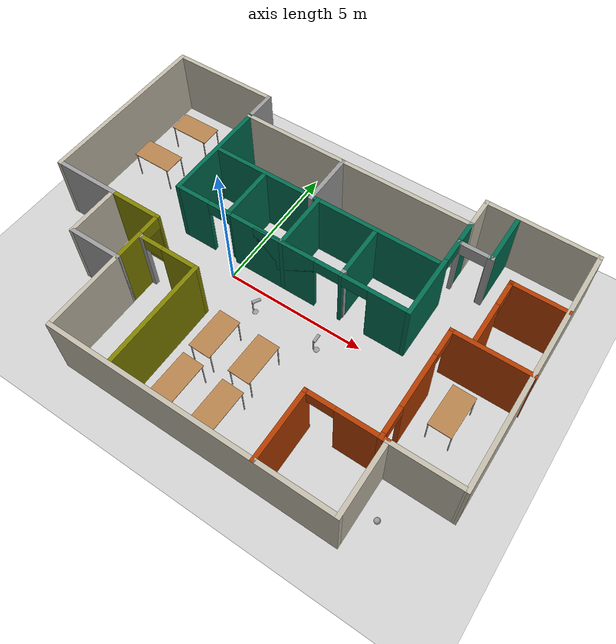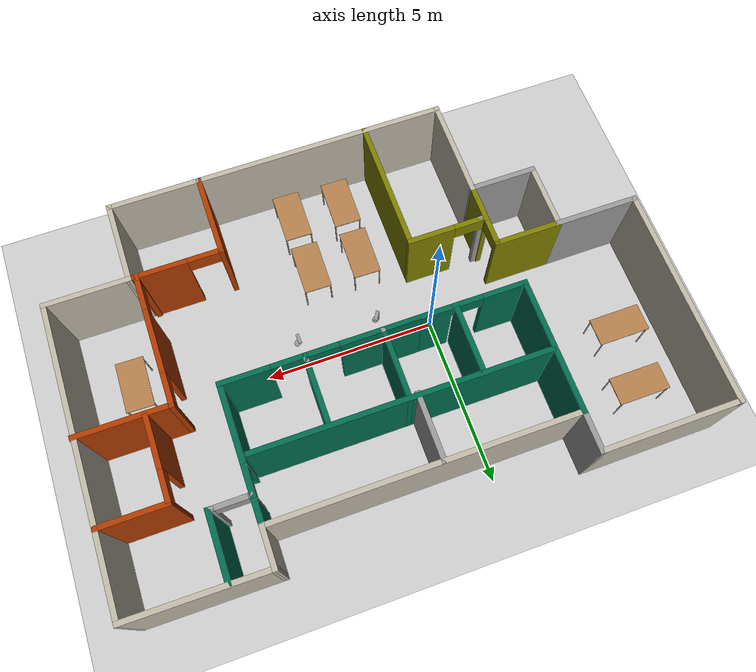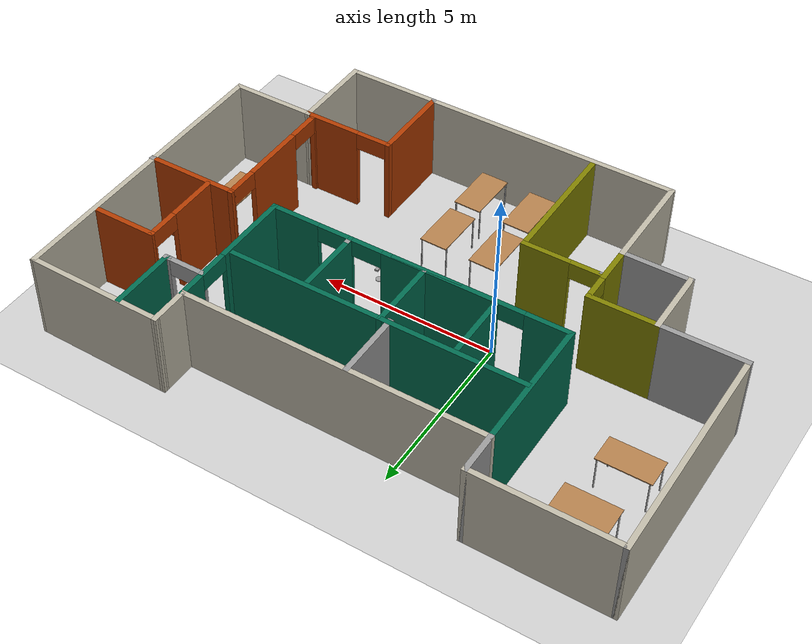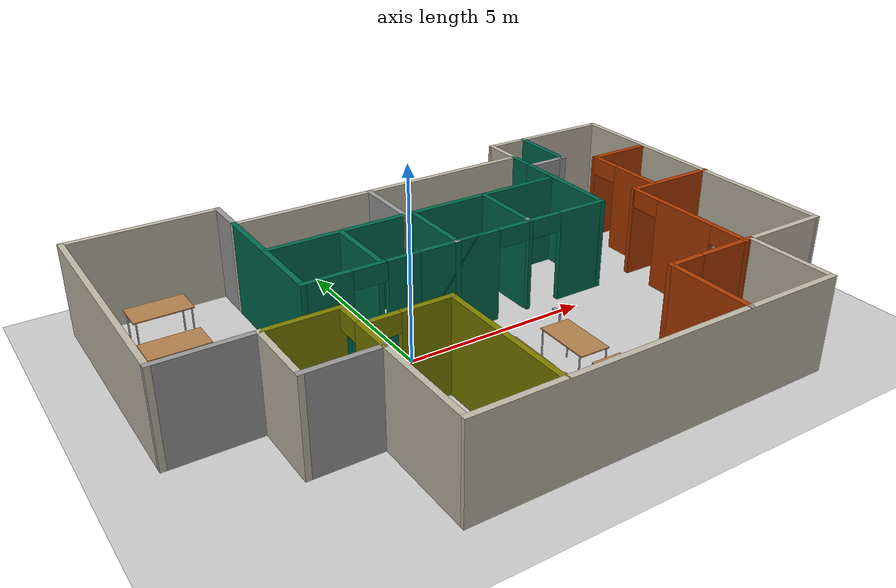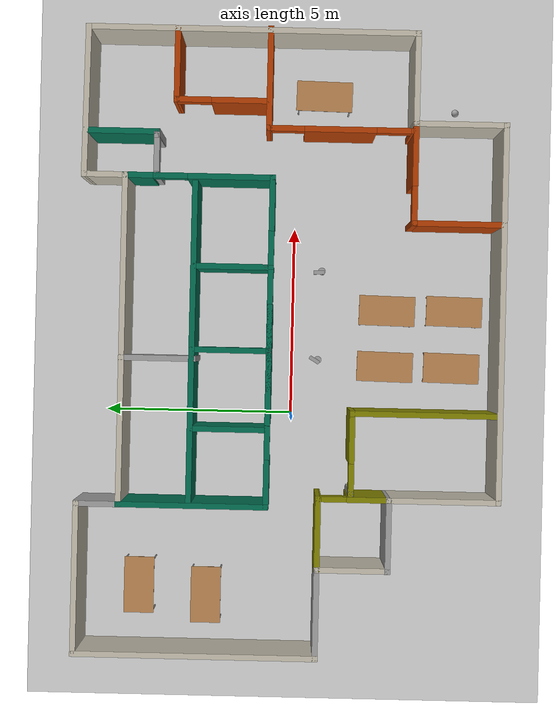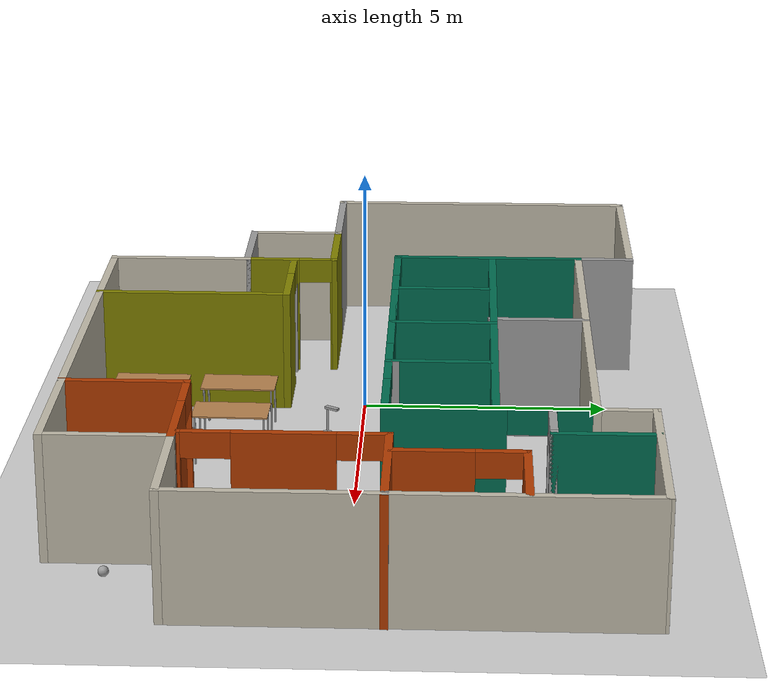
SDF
<sdf version="1.6">
 <world name="default">
  <plugin name="welcome_message" filename="libwelcome_message.so"/>
  <light name="sun" type="directional">
   <pose>0 0 10 0 -0 0</pose>
   <diffuse>0.8 0.8 0.8 1</diffuse>
   <specular>0.2 0.2 0.2 1</specular>
   <attenuation>
    <range>1000</range>
    <constant>0.9</constant>
    <linear>0.01</linear>
    <quadratic>0.001</quadratic>
   </attenuation>
   <direction>-0.5 0.1 -0.9</direction>
  </light>
  <model name="ground_plane">
   <static>1</static>
   <link name="link">
    <collision name="collision">
     <geometry><plane><normal>0 0 1</normal><size>100 100</size></plane></geometry>
     <surface>
      <contact><collide_bitmask>65535</collide_bitmask></contact>
      <friction><ode><mu>100</mu><mu2>50</mu2></ode></friction>
     </surface>
    </collision>
    <visual name="visual">
     <cast_shadows>0</cast_shadows>
     <geometry><plane><normal>0 0 1</normal><size>100 100</size></plane></geometry>
     <material>
      <script><uri>file://media/materials/scripts/gazebo.material</uri><name>Gazebo/Grey</name></script>
     </material>
    </visual>
   </link>
  </model>
  <gravity>0 0 -9.8</gravity>
  <magnetic_field>6e-06 2.3e-05 -4.2e-05</magnetic_field>
  <atmosphere type="adiabatic"/>
  <physics name="default_physics" default="0" type="ode">
   <max_step_size>0.001</max_step_size>
   <real_time_factor>1</real_time_factor>
   <real_time_update_rate>1000</real_time_update_rate>
  </physics>
  <scene><ambient>0.4 0.4 0.4 1</ambient><background>0.7 0.7 0.7 1</background><shadows>1</shadows></scene>
  <spherical_coordinates>
   <surface_model>EARTH_WGS84</surface_model>
   <latitude_deg>0</latitude_deg>
   <longitude_deg>0</longitude_deg>
   <elevation>0</elevation>
   <heading_deg>0</heading_deg>
  </spherical_coordinates>
  <model name="Building">
   <pose>1.88186 0.04983 0 0 -0 0</pose>
   <link name="Wall_10">
    <collision name="Wall_10_Collision">
     <geometry><box><size>4 0.15 2.5</size></box></geometry>
     <pose>0 0 1.25 0 -0 0</pose>
    </collision>
    <visual name="Wall_10_Visual">
     <pose>0 0 1.25 0 -0 0</pose>
     <geometry><box><size>4 0.15 2.5</size></box></geometry>
     <material>
      <script><uri>file://media/materials/scripts/gazebo.material</uri><name>Gazebo/Grey</name></script>
      <ambient>0.745098 0.721569 0.654902 1</ambient>
     </material>
     <meta><layer>0</layer></meta>
    </visual>
    <pose>6.24414 5.46217 0 0 0 -0.011947</pose>
   </link>
   <link name="Wall_11">
    <collision name="Wall_11_Collision">
     <geometry><box><size>8.75 0.15 2.5</size></box></geometry>
     <pose>0 0 1.25 0 -0 0</pose>
    </collision>
    <visual name="Wall_11_Visual">
     <pose>0 0 1.25 0 -0 0</pose>
     <geometry><box><size>8.75 0.15 2.5</size></box></geometry>
     <material>
      <script><uri>file://media/materials/scripts/gazebo.material</uri><name>Gazebo/Grey</name></script>
      <ambient>0.745098 0.721569 0.654902 1</ambient>
     </material>
     <meta><layer>0</layer></meta>
    </visual>
    <pose>8.16914 1.13917 0 0 0 -1.5708</pose>
   </link>
   <link name="Wall_12">
    <collision name="Wall_12_Collision">
     <geometry><box><size>2.5 0.15 2.5</size></box></geometry>
     <pose>0 0 1.25 0 -0 0</pose>
    </collision>
    <visual name="Wall_12_Visual">
     <pose>0 0 1.25 0 -0 0</pose>
     <geometry><box><size>2.5 0.15 2.5</size></box></geometry>
     <material>
      <script><uri>file://media/materials/scripts/gazebo.material</uri><name>Gazebo/Grey</name></script>
      <ambient>0.745098 0.721569 0.654902 1</ambient>
     </material>
     <meta><layer>0</layer></meta>
    </visual>
    <pose>6.99438 -3.1605 0 0 -0 3.14131</pose>
   </link>
   <link name="Wall_13">
    <collision name="Wall_13_Collision">
     <geometry><box><size>2.5 0.15 2.5</size></box></geometry>
     <pose>0 0 1.25 0 -0 0</pose>
    </collision>
    <visual name="Wall_13_Visual">
     <pose>0 0 1.25 0 -0 0</pose>
     <geometry><box><size>2.5 0.15 2.5</size></box></geometry>
     <material>
      <script><uri>file://media/materials/scripts/gazebo.material</uri><name>Gazebo/Grey</name></script>
      <ambient>0.745098 0.721569 0.654902 1</ambient>
     </material>
     <meta><layer>0</layer></meta>
    </visual>
    <pose>5.81961 -4.33517 0 0 0 -1.5708</pose>
   </link>
   <link name="Wall_14">
    <collision name="Wall_14_Collision">
     <geometry><box><size>10 0.15 2.5</size></box></geometry>
     <pose>0 0 1.25 0 -0 0</pose>
    </collision>
    <visual name="Wall_14_Visual">
     <pose>0 0 1.25 0 -0 0</pose>
     <geometry><box><size>10 0.15 2.5</size></box></geometry>
     <material>
      <script><uri>file://media/materials/scripts/gazebo.material</uri><name>Gazebo/Grey</name></script>
      <ambient>0.745098 0.721569 0.654902 1</ambient>
     </material>
     <meta><layer>0</layer></meta>
    </visual>
    <pose>0.894608 -5.51017 0 0 -0 3.14159</pose>
   </link>
   <link name="Wall_15">
    <collision name="Wall_15_Collision">
     <geometry><box><size>3 0.15 2.5</size></box></geometry>
     <pose>0 0 1.25 0 -0 0</pose>
    </collision>
    <visual name="Wall_15_Visual">
     <pose>0 0 1.25 0 -0 0</pose>
     <geometry><box><size>3 0.15 2.5</size></box></geometry>
     <material>
      <script><uri>file://media/materials/scripts/gazebo.material</uri><name>Gazebo/Grey</name></script>
      <ambient>0.745098 0.721569 0.654902 1</ambient>
     </material>
     <meta><layer>0</layer></meta>
    </visual>
    <pose>-4.03062 -4.085 0 0 -0 1.57096</pose>
   </link>
   <link name="Wall_16">
    <collision name="Wall_16_Collision">
     <geometry><box><size>2 0.15 2.5</size></box></geometry>
     <pose>0 0 1.25 0 -0 0</pose>
    </collision>
    <visual name="Wall_16_Visual">
     <pose>0 0 1.25 0 -0 0</pose>
     <geometry><box><size>2 0.15 2.5</size></box></geometry>
     <material>
      <script><uri>file://media/materials/scripts/gazebo.material</uri><name>Gazebo/Grey</name></script>
      <ambient>1 1 1 1</ambient>
     </material>
     <meta><layer>0</layer></meta>
    </visual>
    <pose>-4.95585 -2.65983 0 0 -0 3.14159</pose>
   </link>
   <link name="Wall_17">
    <collision name="Wall_17_Collision">
     <geometry><box><size>2 0.15 2.5</size></box></geometry>
     <pose>0 0 1.25 0 -0 0</pose>
    </collision>
    <visual name="Wall_17_Visual">
     <pose>0 0 1.25 0 -0 0</pose>
     <geometry><box><size>2 0.15 2.5</size></box></geometry>
     <material>
      <script><uri>file://media/materials/scripts/gazebo.material</uri><name>Gazebo/Grey</name></script>
      <ambient>0.745098 0.721569 0.654902 1</ambient>
     </material>
     <meta><layer>0</layer></meta>
    </visual>
    <pose>-5.88086 -1.73483 0 0 -0 1.5708</pose>
   </link>
   <link name="Wall_18">
    <collision name="Wall_18_Collision">
     <geometry><box><size>2.471 0.15 2.5</size></box></geometry>
     <pose>0 0 1.25 0 -0 0</pose>
    </collision>
    <visual name="Wall_18_Visual">
     <pose>0 0 1.25 0 -0 0</pose>
     <geometry><box><size>2.471 0.15 2.5</size></box></geometry>
     <material>
      <script><uri>file://media/materials/scripts/gazebo.material</uri><name>Gazebo/Grey</name></script>
      <ambient>1 1 1 1</ambient>
     </material>
     <meta><layer>0</layer></meta>
    </visual>
    <pose>-7.04136 -0.809827 0 0 -0 3.14159</pose>
   </link>
   <link name="Wall_19">
    <collision name="Wall_19_Collision">
     <geometry><box><size>6.47 0.15 2.5</size></box></geometry>
     <pose>0 0 1.25 0 -0 0</pose>
    </collision>
    <visual name="Wall_19_Visual">
     <pose>0 0 1.25 0 -0 0</pose>
     <geometry><box><size>6.47 0.15 2.5</size></box></geometry>
     <material>
      <script><uri>file://media/materials/scripts/gazebo.material</uri><name>Gazebo/Grey</name></script>
      <ambient>0.745098 0.721569 0.654902 1</ambient>
     </material>
     <meta><layer>0</layer></meta>
    </visual>
    <pose>-8.20186 2.35017 0 0 -0 1.5708</pose>
   </link>
   <link name="Wall_20">
    <collision name="Wall_20_Collision">
     <geometry><box><size>0.15 0.15 2.5</size></box></geometry>
     <pose>0 0 1.25 0 -0 0</pose>
    </collision>
    <visual name="Wall_20_Visual">
     <pose>0 0 1.25 0 -0 0</pose>
     <geometry><box><size>0.15 0.15 2.5</size></box></geometry>
     <material>
      <script><uri>file://media/materials/scripts/gazebo.material</uri><name>Gazebo/Grey</name></script>
      <ambient>1 1 1 1</ambient>
     </material>
     <meta><layer>0</layer></meta>
    </visual>
    <pose>-8.20186 5.51017 0 0 -0 0</pose>
   </link>
   <link name="Wall_22">
    <collision name="Wall_22_Collision">
     <geometry><box><size>2 0.15 2.5</size></box></geometry>
     <pose>0 0 1.25 0 -0 0</pose>
    </collision>
    <visual name="Wall_22_Visual">
     <pose>0 0 1.25 0 -0 0</pose>
     <geometry><box><size>2 0.15 2.5</size></box></geometry>
     <material>
      <script><uri>file://media/materials/scripts/gazebo.material</uri><name>Gazebo/Grey</name></script>
      <ambient>0.498039 0.498039 0 1</ambient>
     </material>
     <meta><layer>0</layer></meta>
    </visual>
    <pose>-4.95585 -0.809827 0 0 -0 0</pose>
   </link>
   <link name="Wall_23">
    <pose>-4.03085 -1.73483 0 0 0 -1.5708</pose>
    <visual name="Wall_23_Visual_0">
     <pose>-0.94307 0 1.25 0 -0 0</pose>
     <geometry><box><size>0.113861 0.15 2.5</size></box></geometry>
     <material>
      <script><uri>file://media/materials/scripts/gazebo.material</uri><name>Gazebo/Grey</name></script>
      <ambient>0.498039 0.498039 0 1</ambient>
     </material>
     <meta><layer>0</layer></meta>
    </visual>
    <collision name="Wall_23_Collision_0">
     <geometry><box><size>0.113861 0.15 2.5</size></box></geometry>
     <pose>-0.94307 0 1.25 0 -0 0</pose>
    </collision>
    <visual name="Wall_23_Visual_1">
     <pose>0.40693 0 1.25 0 -0 0</pose>
     <geometry><box><size>1.18614 0.15 2.5</size></box></geometry>
     <material>
      <script><uri>file://media/materials/scripts/gazebo.material</uri><name>Gazebo/Grey</name></script>
      <ambient>0.498039 0.498039 0 1</ambient>
     </material>
     <meta><layer>0</layer></meta>
    </visual>
    <collision name="Wall_23_Collision_1">
     <geometry><box><size>1.18614 0.15 2.5</size></box></geometry>
     <pose>0.40693 0 1.25 0 -0 0</pose>
    </collision>
    <visual name="Wall_23_Visual_2">
     <pose>-0.536139 0 2.25 0 -0 0</pose>
     <geometry><box><size>0.7 0.15 0.5</size></box></geometry>
     <material>
      <script><uri>file://media/materials/scripts/gazebo.material</uri><name>Gazebo/Grey</name></script>
      <ambient>0.498039 0.498039 0 1</ambient>
     </material>
     <meta><layer>0</layer></meta>
    </visual>
    <collision name="Wall_23_Collision_2">
     <geometry><box><size>0.7 0.15 0.5</size></box></geometry>
     <pose>-0.536139 0 2.25 0 -0 0</pose>
    </collision>
   </link>
   <link name="Wall_24">
    <collision name="Wall_24_Collision">
     <geometry><box><size>0.15 0.15 2.5</size></box></geometry>
     <pose>0 0 1.25 0 -0 0</pose>
    </collision>
    <visual name="Wall_24_Visual">
     <pose>0 0 1.25 0 -0 0</pose>
     <geometry><box><size>0.15 0.15 2.5</size></box></geometry>
     <material>
      <script><uri>file://media/materials/scripts/gazebo.material</uri><name>Gazebo/Grey</name></script>
      <ambient>1 1 1 1</ambient>
     </material>
     <meta><layer>0</layer></meta>
    </visual>
    <pose>-4.03085 -2.65983 0 0 -0 0</pose>
   </link>
   <link name="Wall_28">
    <collision name="Wall_28_Collision">
     <geometry><box><size>4 0.15 2.5</size></box></geometry>
     <pose>0 0 1.25 0 -0 0</pose>
    </collision>
    <visual name="Wall_28_Visual">
     <pose>0 0 1.25 0 -0 0</pose>
     <geometry><box><size>4 0.15 2.5</size></box></geometry>
     <material>
      <script><uri>file://media/materials/scripts/gazebo.material</uri><name>Gazebo/Grey</name></script>
      <ambient>0.498039 0.498039 0 1</ambient>
     </material>
     <meta><layer>0</layer></meta>
    </visual>
    <pose>-1.78286 -3.58433 0 0 -0 1.5708</pose>
   </link>
   <link name="Wall_29">
    <pose>-2.83286 -1.65932 0 0 -0 3.14159</pose>
    <visual name="Wall_29_Visual_0">
     <pose>-0.433114 0 1.25 0 -0 0</pose>
     <geometry><box><size>1.38377 0.15 2.5</size></box></geometry>
     <material>
      <script><uri>file://media/materials/scripts/gazebo.material</uri><name>Gazebo/Grey</name></script>
      <ambient>0.498039 0.498039 0 1</ambient>
     </material>
     <meta><layer>0</layer></meta>
    </visual>
    <collision name="Wall_29_Collision_0">
     <geometry><box><size>1.38377 0.15 2.5</size></box></geometry>
     <pose>-0.433114 0 1.25 0 -0 0</pose>
    </collision>
    <visual name="Wall_29_Visual_1">
     <pose>0.691886 0 2.25 0 -0 0</pose>
     <geometry><box><size>0.866229 0.15 0.5</size></box></geometry>
     <material>
      <script><uri>file://media/materials/scripts/gazebo.material</uri><name>Gazebo/Grey</name></script>
      <ambient>0.498039 0.498039 0 1</ambient>
     </material>
     <meta><layer>0</layer></meta>
    </visual>
    <collision name="Wall_29_Collision_1">
     <geometry><box><size>0.866229 0.15 0.5</size></box></geometry>
     <pose>0.691886 0 2.25 0 -0 0</pose>
    </collision>
   </link>
   <link name="Wall_30">
    <collision name="Wall_30_Collision">
     <geometry><box><size>0.16 0.15 2.5</size></box></geometry>
     <pose>0 0 1.25 0 -0 0</pose>
    </collision>
    <visual name="Wall_30_Visual">
     <pose>0 0 1.25 0 -0 0</pose>
     <geometry><box><size>0.16 0.15 2.5</size></box></geometry>
     <material>
      <script><uri>file://media/materials/scripts/gazebo.material</uri><name>Gazebo/Grey</name></script>
      <ambient>1 1 1 1</ambient>
     </material>
     <meta><layer>0</layer></meta>
    </visual>
    <pose>-3.87786 -1.65932 0 0 -0 0</pose>
   </link>
   <link name="Wall_32">
    <pose>4.51961 -3.16017 0 0 -0 3.14159</pose>
    <visual name="Wall_32_Visual_0">
     <pose>-0.522117 0 1.25 0 -0 0</pose>
     <geometry><box><size>1.70577 0.15 2.5</size></box></geometry>
     <material>
      <script><uri>file://media/materials/scripts/gazebo.material</uri><name>Gazebo/Grey</name></script>
      <ambient>0.686275 0.227451 0 1</ambient>
     </material>
     <meta><layer>0</layer></meta>
    </visual>
    <collision name="Wall_32_Collision_0">
     <geometry><box><size>1.70577 0.15 2.5</size></box></geometry>
     <pose>-0.522117 0 1.25 0 -0 0</pose>
    </collision>
    <visual name="Wall_32_Visual_1">
     <pose>1.30288 0 1.25 0 -0 0</pose>
     <geometry><box><size>0.144234 0.15 2.5</size></box></geometry>
     <material>
      <script><uri>file://media/materials/scripts/gazebo.material</uri><name>Gazebo/Grey</name></script>
      <ambient>0.686275 0.227451 0 1</ambient>
     </material>
     <meta><layer>0</layer></meta>
    </visual>
    <collision name="Wall_32_Collision_1">
     <geometry><box><size>0.144234 0.15 2.5</size></box></geometry>
     <pose>1.30288 0 1.25 0 -0 0</pose>
    </collision>
    <visual name="Wall_32_Visual_2">
     <pose>0.780766 0 2.25 0 -0 0</pose>
     <geometry><box><size>0.9 0.15 0.5</size></box></geometry>
     <material>
      <script><uri>file://media/materials/scripts/gazebo.material</uri><name>Gazebo/Grey</name></script>
      <ambient>0.686275 0.227451 0 1</ambient>
     </material>
     <meta><layer>0</layer></meta>
    </visual>
    <collision name="Wall_32_Collision_2">
     <geometry><box><size>0.9 0.15 0.5</size></box></geometry>
     <pose>0.780766 0 2.25 0 -0 0</pose>
    </collision>
   </link>
   <link name="Wall_33">
    <collision name="Wall_33_Collision">
     <geometry><box><size>2.5 0.15 2.5</size></box></geometry>
     <pose>0 0 1.25 0 -0 0</pose>
    </collision>
    <visual name="Wall_33_Visual">
     <pose>0 0 1.25 0 -0 0</pose>
     <geometry><box><size>2.5 0.15 2.5</size></box></geometry>
     <material>
      <script><uri>file://media/materials/scripts/gazebo.material</uri><name>Gazebo/Grey</name></script>
      <ambient>0.686275 0.227451 0 1</ambient>
     </material>
     <meta><layer>0</layer></meta>
    </visual>
    <pose>3.21961 -4.33517 0 0 0 -1.5708</pose>
   </link>
   <link name="Wall_34">
    <collision name="Wall_34_Collision">
     <geometry><box><size>0.15 0.15 2.5</size></box></geometry>
     <pose>0 0 1.25 0 -0 0</pose>
    </collision>
    <visual name="Wall_34_Visual">
     <pose>0 0 1.25 0 -0 0</pose>
     <geometry><box><size>0.15 0.15 2.5</size></box></geometry>
     <material>
      <script><uri>file://media/materials/scripts/gazebo.material</uri><name>Gazebo/Grey</name></script>
      <ambient>1 1 1 1</ambient>
     </material>
     <meta><layer>0</layer></meta>
    </visual>
    <pose>3.21961 -5.51017 0 0 -0 0</pose>
   </link>
   <link name="Wall_36">
    <pose>5.61815 -1.23783 0 0 -0 1.5708</pose>
    <visual name="Wall_36_Visual_0">
     <pose>-1.89371 0 1.25 0 -0 0</pose>
     <geometry><box><size>0.212579 0.15 2.5</size></box></geometry>
     <material>
      <script><uri>file://media/materials/scripts/gazebo.material</uri><name>Gazebo/Grey</name></script>
      <ambient>0.686275 0.227451 0 1</ambient>
     </material>
     <meta><layer>0</layer></meta>
    </visual>
    <collision name="Wall_36_Collision_0">
     <geometry><box><size>0.212579 0.15 2.5</size></box></geometry>
     <pose>-1.89371 0 1.25 0 -0 0</pose>
    </collision>
    <visual name="Wall_36_Visual_1">
     <pose>0.054434 0 1.25 0 -0 0</pose>
     <geometry><box><size>1.88371 0.15 2.5</size></box></geometry>
     <material>
      <script><uri>file://media/materials/scripts/gazebo.material</uri><name>Gazebo/Grey</name></script>
      <ambient>0.686275 0.227451 0 1</ambient>
     </material>
     <meta><layer>0</layer></meta>
    </visual>
    <collision name="Wall_36_Collision_1">
     <geometry><box><size>1.88371 0.15 2.5</size></box></geometry>
     <pose>0.054434 0 1.25 0 -0 0</pose>
    </collision>
    <visual name="Wall_36_Visual_2">
     <pose>1.94815 0 1.25 0 -0 0</pose>
     <geometry><box><size>0.10371 0.15 2.5</size></box></geometry>
     <material>
      <script><uri>file://media/materials/scripts/gazebo.material</uri><name>Gazebo/Grey</name></script>
      <ambient>0.686275 0.227451 0 1</ambient>
     </material>
     <meta><layer>0</layer></meta>
    </visual>
    <collision name="Wall_36_Collision_2">
     <geometry><box><size>0.10371 0.15 2.5</size></box></geometry>
     <pose>1.94815 0 1.25 0 -0 0</pose>
    </collision>
    <visual name="Wall_36_Visual_3">
     <pose>-1.33742 0 2.25 0 -0 0</pose>
     <geometry><box><size>0.9 0.15 0.5</size></box></geometry>
     <material>
      <script><uri>file://media/materials/scripts/gazebo.material</uri><name>Gazebo/Grey</name></script>
      <ambient>0.686275 0.227451 0 1</ambient>
     </material>
     <meta><layer>0</layer></meta>
    </visual>
    <collision name="Wall_36_Collision_3">
     <geometry><box><size>0.9 0.15 0.5</size></box></geometry>
     <pose>-1.33742 0 2.25 0 -0 0</pose>
    </collision>
    <visual name="Wall_36_Visual_4">
     <pose>1.44629 0 2.25 0 -0 0</pose>
     <geometry><box><size>0.9 0.15 0.5</size></box></geometry>
     <material>
      <script><uri>file://media/materials/scripts/gazebo.material</uri><name>Gazebo/Grey</name></script>
      <ambient>0.686275 0.227451 0 1</ambient>
     </material>
     <meta><layer>0</layer></meta>
    </visual>
    <collision name="Wall_36_Collision_4">
     <geometry><box><size>0.9 0.15 0.5</size></box></geometry>
     <pose>1.44629 0 2.25 0 -0 0</pose>
    </collision>
   </link>
   <link name="Wall_37">
    <collision name="Wall_37_Collision">
     <geometry><box><size>2.73371 0.15 2.5</size></box></geometry>
     <pose>0 0 1.25 0 -0 0</pose>
    </collision>
    <visual name="Wall_37_Visual">
     <pose>0 0 1.25 0 -0 0</pose>
     <geometry><box><size>2.73371 0.15 2.5</size></box></geometry>
     <material>
      <script><uri>file://media/materials/scripts/gazebo.material</uri><name>Gazebo/Grey</name></script>
      <ambient>0.686275 0.227451 0 1</ambient>
     </material>
     <meta><layer>0</layer></meta>
    </visual>
    <pose>6.91 0.687136 0 0 0 -2.9e-05</pose>
   </link>
   <link name="Wall_38">
    <collision name="Wall_38_Collision">
     <geometry><box><size>0.15 0.15 2.5</size></box></geometry>
     <pose>0 0 1.25 0 -0 0</pose>
    </collision>
    <visual name="Wall_38_Visual">
     <pose>0 0 1.25 0 -0 0</pose>
     <geometry><box><size>0.15 0.15 2.5</size></box></geometry>
     <material>
      <script><uri>file://media/materials/scripts/gazebo.material</uri><name>Gazebo/Grey</name></script>
      <ambient>1 1 1 1</ambient>
     </material>
     <meta><layer>0</layer></meta>
    </visual>
    <pose>8.20185 0.687099 0 0 -0 0</pose>
   </link>
   <link name="Wall_40">
    <pose>6.31814 1.93617 0 0 -0 1.5708</pose>
    <visual name="Wall_40_Visual_0">
     <pose>-0.490246 0 1.25 0 -0 0</pose>
     <geometry><box><size>1.51951 0.15 2.5</size></box></geometry>
     <material>
      <script><uri>file://media/materials/scripts/gazebo.material</uri><name>Gazebo/Grey</name></script>
      <ambient>0.686275 0.227451 0 1</ambient>
     </material>
     <meta><layer>0</layer></meta>
    </visual>
    <collision name="Wall_40_Collision_0">
     <geometry><box><size>1.51951 0.15 2.5</size></box></geometry>
     <pose>-0.490246 0 1.25 0 -0 0</pose>
    </collision>
    <visual name="Wall_40_Visual_1">
     <pose>1.20975 0 1.25 0 -0 0</pose>
     <geometry><box><size>0.080492 0.15 2.5</size></box></geometry>
     <material>
      <script><uri>file://media/materials/scripts/gazebo.material</uri><name>Gazebo/Grey</name></script>
      <ambient>0.686275 0.227451 0 1</ambient>
     </material>
     <meta><layer>0</layer></meta>
    </visual>
    <collision name="Wall_40_Collision_1">
     <geometry><box><size>0.080492 0.15 2.5</size></box></geometry>
     <pose>1.20975 0 1.25 0 -0 0</pose>
    </collision>
    <visual name="Wall_40_Visual_2">
     <pose>0.719508 0 2.25 0 -0 0</pose>
     <geometry><box><size>0.9 0.15 0.5</size></box></geometry>
     <material>
      <script><uri>file://media/materials/scripts/gazebo.material</uri><name>Gazebo/Grey</name></script>
      <ambient>0.686275 0.227451 0 1</ambient>
     </material>
     <meta><layer>0</layer></meta>
    </visual>
    <collision name="Wall_40_Collision_2">
     <geometry><box><size>0.9 0.15 0.5</size></box></geometry>
     <pose>0.719508 0 2.25 0 -0 0</pose>
    </collision>
   </link>
   <link name="Wall_41">
    <collision name="Wall_41_Collision">
     <geometry><box><size>2.001 0.15 2.5</size></box></geometry>
     <pose>0 0 1.25 0 -0 0</pose>
    </collision>
    <visual name="Wall_41_Visual">
     <pose>0 0 1.25 0 -0 0</pose>
     <geometry><box><size>2.001 0.15 2.5</size></box></geometry>
     <material>
      <script><uri>file://media/materials/scripts/gazebo.material</uri><name>Gazebo/Grey</name></script>
      <ambient>0.686275 0.227451 0 1</ambient>
     </material>
     <meta><layer>0</layer></meta>
    </visual>
    <pose>7.24364 3.11117 0 0 -0 0</pose>
   </link>
   <link name="Wall_44">
    <collision name="Wall_44_Collision">
     <geometry><box><size>0.15 0.15 2.5</size></box></geometry>
     <pose>0 0 1.25 0 -0 0</pose>
    </collision>
    <visual name="Wall_44_Visual">
     <pose>0 0 1.25 0 -0 0</pose>
     <geometry><box><size>0.15 0.15 2.5</size></box></geometry>
     <material>
      <script><uri>file://media/materials/scripts/gazebo.material</uri><name>Gazebo/Grey</name></script>
      <ambient>1 1 1 1</ambient>
     </material>
     <meta><layer>0</layer></meta>
    </visual>
    <pose>5.37778 3.60414 0 0 -0 0</pose>
   </link>
   <link name="Wall_46">
    <collision name="Wall_46_Collision">
     <geometry><box><size>4 0.15 2.5</size></box></geometry>
     <pose>0 0 1.25 0 -0 0</pose>
    </collision>
    <visual name="Wall_46_Visual">
     <pose>0 0 1.25 0 -0 0</pose>
     <geometry><box><size>4 0.15 2.5</size></box></geometry>
     <material>
      <script><uri>file://media/materials/scripts/gazebo.material</uri><name>Gazebo/Grey</name></script>
      <ambient>0 0.415686 0.305882 1</ambient>
     </material>
     <meta><layer>0</layer></meta>
    </visual>
    <pose>-4.28085 2.48517 0 0 0 -1.5708</pose>
   </link>
   <link name="Wall_47">
    <pose>0.019145 0.560173 0 0 -0 0</pose>
    <visual name="Wall_47_Visual_0">
     <pose>-3.71874 0 1.25 0 -0 0</pose>
     <geometry><box><size>1.31252 0.15 2.5</size></box></geometry>
     <material>
      <script><uri>file://media/materials/scripts/gazebo.material</uri><name>Gazebo/Grey</name></script>
      <ambient>0 0.415686 0.305882 1</ambient>
     </material>
     <meta><layer>0</layer></meta>
    </visual>
    <collision name="Wall_47_Collision_0">
     <geometry><box><size>1.31252 0.15 2.5</size></box></geometry>
     <pose>-3.71874 0 1.25 0 -0 0</pose>
    </collision>
    <visual name="Wall_47_Visual_1">
     <pose>-0.57823 0 1.25 0 -0 0</pose>
     <geometry><box><size>3.1685 0.15 2.5</size></box></geometry>
     <material>
      <script><uri>file://media/materials/scripts/gazebo.material</uri><name>Gazebo/Grey</name></script>
      <ambient>0 0.415686 0.305882 1</ambient>
     </material>
     <meta><layer>0</layer></meta>
    </visual>
    <collision name="Wall_47_Collision_1">
     <geometry><box><size>3.1685 0.15 2.5</size></box></geometry>
     <pose>-0.57823 0 1.25 0 -0 0</pose>
    </collision>
    <visual name="Wall_47_Visual_2">
     <pose>-0.134671 0 1.25 0 -0 0</pose>
     <geometry><box><size>2.28138 0.15 2.5</size></box></geometry>
     <material>
      <script><uri>file://media/materials/scripts/gazebo.material</uri><name>Gazebo/Grey</name></script>
      <ambient>0 0.415686 0.305882 1</ambient>
     </material>
     <meta><layer>0</layer></meta>
    </visual>
    <collision name="Wall_47_Collision_2">
     <geometry><box><size>2.28138 0.15 2.5</size></box></geometry>
     <pose>-0.134671 0 1.25 0 -0 0</pose>
    </collision>
    <visual name="Wall_47_Visual_3">
     <pose>1.96076 0 1.25 0 -0 0</pose>
     <geometry><box><size>0.109477 0.15 2.5</size></box></geometry>
     <material>
      <script><uri>file://media/materials/scripts/gazebo.material</uri><name>Gazebo/Grey</name></script>
      <ambient>0 0.415686 0.305882 1</ambient>
     </material>
     <meta><layer>0</layer></meta>
    </visual>
    <collision name="Wall_47_Collision_3">
     <geometry><box><size>0.109477 0.15 2.5</size></box></geometry>
     <pose>1.96076 0 1.25 0 -0 0</pose>
    </collision>
    <visual name="Wall_47_Visual_4">
     <pose>3.64525 0 1.25 0 -0 0</pose>
     <geometry><box><size>1.4595 0.15 2.5</size></box></geometry>
     <material>
      <script><uri>file://media/materials/scripts/gazebo.material</uri><name>Gazebo/Grey</name></script>
      <ambient>0 0.415686 0.305882 1</ambient>
     </material>
     <meta><layer>0</layer></meta>
    </visual>
    <collision name="Wall_47_Collision_4">
     <geometry><box><size>1.4595 0.15 2.5</size></box></geometry>
     <pose>3.64525 0 1.25 0 -0 0</pose>
    </collision>
    <visual name="Wall_47_Visual_5">
     <pose>-2.61892 0 2.25 0 -0 0</pose>
     <geometry><box><size>0.887117 0.15 0.5</size></box></geometry>
     <material>
      <script><uri>file://media/materials/scripts/gazebo.material</uri><name>Gazebo/Grey</name></script>
      <ambient>0 0.415686 0.305882 1</ambient>
     </material>
     <meta><layer>0</layer></meta>
    </visual>
    <collision name="Wall_47_Collision_5">
     <geometry><box><size>0.887117 0.15 0.5</size></box></geometry>
     <pose>-2.61892 0 2.25 0 -0 0</pose>
    </collision>
    <visual name="Wall_47_Visual_6">
     <pose>1.45602 0 2.25 0 -0 0</pose>
     <geometry><box><size>0.9 0.15 0.5</size></box></geometry>
     <material>
      <script><uri>file://media/materials/scripts/gazebo.material</uri><name>Gazebo/Grey</name></script>
      <ambient>0 0.415686 0.305882 1</ambient>
     </material>
     <meta><layer>0</layer></meta>
    </visual>
    <collision name="Wall_47_Collision_6">
     <geometry><box><size>0.9 0.15 0.5</size></box></geometry>
     <pose>1.45602 0 2.25 0 -0 0</pose>
    </collision>
    <visual name="Wall_47_Visual_7">
     <pose>1.45602 0 2.25 0 -0 0</pose>
     <geometry><box><size>0.9 0.15 0.5</size></box></geometry>
     <material>
      <script><uri>file://media/materials/scripts/gazebo.material</uri><name>Gazebo/Grey</name></script>
      <ambient>0 0.415686 0.305882 1</ambient>
     </material>
     <meta><layer>0</layer></meta>
    </visual>
    <collision name="Wall_47_Collision_7">
     <geometry><box><size>0.9 0.15 0.5</size></box></geometry>
     <pose>1.45602 0 2.25 0 -0 0</pose>
    </collision>
    <visual name="Wall_47_Visual_8">
     <pose>2.4655 0 2.25 0 -0 0</pose>
     <geometry><box><size>0.9 0.15 0.5</size></box></geometry>
     <material>
      <script><uri>file://media/materials/scripts/gazebo.material</uri><name>Gazebo/Grey</name></script>
      <ambient>0 0.415686 0.305882 1</ambient>
     </material>
     <meta><layer>0</layer></meta>
    </visual>
    <collision name="Wall_47_Collision_8">
     <geometry><box><size>0.9 0.15 0.5</size></box></geometry>
     <pose>2.4655 0 2.25 0 -0 0</pose>
    </collision>
   </link>
   <link name="Wall_48">
    <pose>4.31914 2.48517 0 0 -0 1.5708</pose>
    <visual name="Wall_48_Visual_0">
     <pose>-0.849139 0 1.25 0 -0 0</pose>
     <geometry><box><size>2.30172 0.15 2.5</size></box></geometry>
     <material>
      <script><uri>file://media/materials/scripts/gazebo.material</uri><name>Gazebo/Grey</name></script>
      <ambient>0 0.415686 0.305882 1</ambient>
     </material>
     <meta><layer>0</layer></meta>
    </visual>
    <collision name="Wall_48_Collision_0">
     <geometry><box><size>2.30172 0.15 2.5</size></box></geometry>
     <pose>-0.849139 0 1.25 0 -0 0</pose>
    </collision>
    <visual name="Wall_48_Visual_1">
     <pose>1.60086 0 1.25 0 -0 0</pose>
     <geometry><box><size>0.798278 0.15 2.5</size></box></geometry>
     <material>
      <script><uri>file://media/materials/scripts/gazebo.material</uri><name>Gazebo/Grey</name></script>
      <ambient>0 0.415686 0.305882 1</ambient>
     </material>
     <meta><layer>0</layer></meta>
    </visual>
    <collision name="Wall_48_Collision_1">
     <geometry><box><size>0.798278 0.15 2.5</size></box></geometry>
     <pose>1.60086 0 1.25 0 -0 0</pose>
    </collision>
    <visual name="Wall_48_Visual_2">
     <pose>0.751722 0 2.25 0 -0 0</pose>
     <geometry><box><size>0.9 0.15 0.5</size></box></geometry>
     <material>
      <script><uri>file://media/materials/scripts/gazebo.material</uri><name>Gazebo/Grey</name></script>
      <ambient>0 0.415686 0.305882 1</ambient>
     </material>
     <meta><layer>0</layer></meta>
    </visual>
    <collision name="Wall_48_Collision_2">
     <geometry><box><size>0.9 0.15 0.5</size></box></geometry>
     <pose>0.751722 0 2.25 0 -0 0</pose>
    </collision>
   </link>
   <link name="Wall_49">
    <collision name="Wall_49_Collision">
     <geometry><box><size>0.15 0.15 2.5</size></box></geometry>
     <pose>0 0 1.25 0 -0 0</pose>
    </collision>
    <visual name="Wall_49_Visual">
     <pose>0 0 1.25 0 -0 0</pose>
     <geometry><box><size>0.15 0.15 2.5</size></box></geometry>
     <material>
      <script><uri>file://media/materials/scripts/gazebo.material</uri><name>Gazebo/Grey</name></script>
      <ambient>1 1 1 1</ambient>
     </material>
     <meta><layer>0</layer></meta>
    </visual>
    <pose>4.31914 4.41017 0 0 -0 0</pose>
   </link>
   <link name="Wall_51">
    <collision name="Wall_51_Collision">
     <geometry><box><size>8.5 0.15 2.5</size></box></geometry>
     <pose>0 0 1.25 0 -0 0</pose>
    </collision>
    <visual name="Wall_51_Visual">
     <pose>0 0 1.25 0 -0 0</pose>
     <geometry><box><size>8.5 0.15 2.5</size></box></geometry>
     <material>
      <script><uri>file://media/materials/scripts/gazebo.material</uri><name>Gazebo/Grey</name></script>
      <ambient>0 0.415686 0.305882 1</ambient>
     </material>
     <meta><layer>0</layer></meta>
    </visual>
    <pose>-0.033774 2.57779 0 0 -0 0</pose>
   </link>
   <link name="Wall_53">
    <collision name="Wall_53_Collision">
     <geometry><box><size>2 0.15 2.5</size></box></geometry>
     <pose>0 0 1.25 0 -0 0</pose>
    </collision>
    <visual name="Wall_53_Visual">
     <pose>0 0 1.25 0 -0 0</pose>
     <geometry><box><size>2 0.15 2.5</size></box></geometry>
     <material>
      <script><uri>file://media/materials/scripts/gazebo.material</uri><name>Gazebo/Grey</name></script>
      <ambient>0 0.415686 0.305882 1</ambient>
     </material>
     <meta><layer>0</layer></meta>
    </visual>
    <pose>-2.26691 1.61234 0 0 0 -1.5708</pose>
   </link>
   <link name="Wall_57">
    <collision name="Wall_57_Collision">
     <geometry><box><size>2 0.15 2.5</size></box></geometry>
     <pose>0 0 1.25 0 -0 0</pose>
    </collision>
    <visual name="Wall_57_Visual">
     <pose>0 0 1.25 0 -0 0</pose>
     <geometry><box><size>2 0.15 2.5</size></box></geometry>
     <material>
      <script><uri>file://media/materials/scripts/gazebo.material</uri><name>Gazebo/Grey</name></script>
      <ambient>0 0.415686 0.305882 1</ambient>
     </material>
     <meta><layer>0</layer></meta>
    </visual>
    <pose>1.98093 1.61234 0 0 0 -1.5708</pose>
   </link>
   <link name="Wall_58">
    <collision name="Wall_58_Collision">
     <geometry><box><size>0.15 0.15 2.5</size></box></geometry>
     <pose>0 0 1.25 0 -0 0</pose>
    </collision>
    <visual name="Wall_58_Visual">
     <pose>0 0 1.25 0 -0 0</pose>
     <geometry><box><size>0.15 0.15 2.5</size></box></geometry>
     <material>
      <script><uri>file://media/materials/scripts/gazebo.material</uri><name>Gazebo/Grey</name></script>
      <ambient>1 1 1 1</ambient>
     </material>
     <meta><layer>0</layer></meta>
    </visual>
    <pose>1.98093 0.687335 0 0 -0 0</pose>
   </link>
   <link name="Wall_6">
    <collision name="Wall_6_Collision">
     <geometry><box><size>4.071 0.15 2.5</size></box></geometry>
     <pose>0 0 1.25 0 -0 0</pose>
    </collision>
    <visual name="Wall_6_Visual">
     <pose>0 0 1.25 0 -0 0</pose>
     <geometry><box><size>4.071 0.15 2.5</size></box></geometry>
     <material>
      <script><uri>file://media/materials/scripts/gazebo.material</uri><name>Gazebo/Grey</name></script>
      <ambient>0.745098 0.721569 0.654902 1</ambient>
     </material>
     <meta><layer>0</layer></meta>
    </visual>
    <pose>-6.24136 5.51017 0 0 -0 0</pose>
   </link>
   <link name="Wall_60">
    <collision name="Wall_60_Collision">
     <geometry><box><size>2.011 0.15 2.5</size></box></geometry>
     <pose>0 0 1.25 0 -0 0</pose>
    </collision>
    <visual name="Wall_60_Visual">
     <pose>0 0 1.25 0 -0 0</pose>
     <geometry><box><size>2.011 0.15 2.5</size></box></geometry>
     <material>
      <script><uri>file://media/materials/scripts/gazebo.material</uri><name>Gazebo/Grey</name></script>
      <ambient>1 1 1 1</ambient>
     </material>
     <meta><layer>0</layer></meta>
    </visual>
    <pose>-0.446856 3.46767 0 0 0 -1.5708</pose>
   </link>
   <link name="Wall_62">
    <collision name="Wall_62_Collision">
     <geometry><box><size>2.168 0.15 2.5</size></box></geometry>
     <pose>0 0 1.25 0 -0 0</pose>
    </collision>
    <visual name="Wall_62_Visual">
     <pose>0 0 1.25 0 -0 0</pose>
     <geometry><box><size>2.168 0.15 2.5</size></box></geometry>
     <material>
      <script><uri>file://media/materials/scripts/gazebo.material</uri><name>Gazebo/Grey</name></script>
      <ambient>0 0.415686 0.305882 1</ambient>
     </material>
     <meta><layer>0</layer></meta>
    </visual>
    <pose>-0.203856 1.56917 0 0 0 -1.5708</pose>
   </link>
   <link name="Wall_63">
    <collision name="Wall_63_Collision">
     <geometry><box><size>0.15 0.15 2.5</size></box></geometry>
     <pose>0 0 1.25 0 -0 0</pose>
    </collision>
    <visual name="Wall_63_Visual">
     <pose>0 0 1.25 0 -0 0</pose>
     <geometry><box><size>0.15 0.15 2.5</size></box></geometry>
     <material>
      <script><uri>file://media/materials/scripts/gazebo.material</uri><name>Gazebo/Grey</name></script>
      <ambient>1 1 1 1</ambient>
     </material>
     <meta><layer>0</layer></meta>
    </visual>
    <pose>-0.203856 0.560173 0 0 -0 0</pose>
   </link>
   <link name="Wall_65">
    <collision name="Wall_65_Collision">
     <geometry><box><size>2 0.15 2.5</size></box></geometry>
     <pose>0 0 1.25 0 -0 0</pose>
    </collision>
    <visual name="Wall_65_Visual">
     <pose>0 0 1.25 0 -0 0</pose>
     <geometry><box><size>2 0.15 2.5</size></box></geometry>
     <material>
      <script><uri>file://media/materials/scripts/gazebo.material</uri><name>Gazebo/Grey</name></script>
      <ambient>0 0.415686 0.305882 1</ambient>
     </material>
     <meta><layer>0</layer></meta>
    </visual>
    <pose>5.46011 4.52514 0 0 0 -1.5708</pose>
   </link>
   <link name="Wall_66">
    <pose>4.91011 3.60014 0 0 -0 3.14159</pose>
    <visual name="Wall_66_Visual_0">
     <pose>-0.517786 0 1.25 0 -0 0</pose>
     <geometry><box><size>0.214428 0.15 2.5</size></box></geometry>
     <material>
      <script><uri>file://media/materials/scripts/gazebo.material</uri><name>Gazebo/Grey</name></script>
      <ambient>1 1 1 1</ambient>
     </material>
     <meta><layer>0</layer></meta>
    </visual>
    <collision name="Wall_66_Collision_0">
     <geometry><box><size>0.214428 0.15 2.5</size></box></geometry>
     <pose>-0.517786 0 1.25 0 -0 0</pose>
    </collision>
    <visual name="Wall_66_Visual_1">
     <pose>0.557214 0 1.25 0 -0 0</pose>
     <geometry><box><size>0.135572 0.15 2.5</size></box></geometry>
     <material>
      <script><uri>file://media/materials/scripts/gazebo.material</uri><name>Gazebo/Grey</name></script>
      <ambient>1 1 1 1</ambient>
     </material>
     <meta><layer>0</layer></meta>
    </visual>
    <collision name="Wall_66_Collision_1">
     <geometry><box><size>0.135572 0.15 2.5</size></box></geometry>
     <pose>0.557214 0 1.25 0 -0 0</pose>
    </collision>
    <visual name="Wall_66_Visual_2">
     <pose>0.039428 0 2.25 0 -0 0</pose>
     <geometry><box><size>0.9 0.15 0.5</size></box></geometry>
     <material>
      <script><uri>file://media/materials/scripts/gazebo.material</uri><name>Gazebo/Grey</name></script>
      <ambient>1 1 1 1</ambient>
     </material>
     <meta><layer>0</layer></meta>
    </visual>
    <collision name="Wall_66_Collision_2">
     <geometry><box><size>0.9 0.15 0.5</size></box></geometry>
     <pose>0.039428 0 2.25 0 -0 0</pose>
    </collision>
   </link>
   <link name="Wall_7">
    <collision name="Wall_7_Collision">
     <geometry><box><size>1.25 0.15 2.5</size></box></geometry>
     <pose>0 0 1.25 0 -0 0</pose>
    </collision>
    <visual name="Wall_7_Visual">
     <pose>0 0 1.25 0 -0 0</pose>
     <geometry><box><size>1.25 0.15 2.5</size></box></geometry>
     <material>
      <script><uri>file://media/materials/scripts/gazebo.material</uri><name>Gazebo/Grey</name></script>
      <ambient>1 1 1 1</ambient>
     </material>
     <meta><layer>0</layer></meta>
    </visual>
    <pose>-4.28085 4.96017 0 0 0 -1.5708</pose>
   </link>
   <link name="Wall_8">
    <collision name="Wall_8_Collision">
     <geometry><box><size>8.75 0.15 2.5</size></box></geometry>
     <pose>0 0 1.25 0 -0 0</pose>
    </collision>
    <visual name="Wall_8_Visual">
     <pose>0 0 1.25 0 -0 0</pose>
     <geometry><box><size>8.75 0.15 2.5</size></box></geometry>
     <material>
      <script><uri>file://media/materials/scripts/gazebo.material</uri><name>Gazebo/Grey</name></script>
      <ambient>0.745098 0.721569 0.654902 1</ambient>
     </material>
     <meta><layer>0</layer></meta>
    </visual>
    <pose>0.019145 4.41017 0 0 -0 0</pose>
   </link>
   <link name="Wall_9">
    <collision name="Wall_9_Collision">
     <geometry><box><size>1.225 0.15 2.5</size></box></geometry>
     <pose>0 0 1.25 0 -0 0</pose>
    </collision>
    <visual name="Wall_9_Visual">
     <pose>0 0 1.25 0 -0 0</pose>
     <geometry><box><size>1.225 0.15 2.5</size></box></geometry>
     <material>
      <script><uri>file://media/materials/scripts/gazebo.material</uri><name>Gazebo/Grey</name></script>
      <ambient>0.745098 0.721569 0.654902 1</ambient>
     </material>
     <meta><layer>0</layer></meta>
    </visual>
    <pose>4.31914 4.94767 0 0 -0 1.5708</pose>
   </link>
   <static>1</static>
  </model>
  <model name="table">
   <static>1</static>
   <link name="link">
    <collision name="surface">
     <pose>0 0 1 0 -0 0</pose>
     <geometry><box><size>1.5 0.8 0.03</size></box></geometry>
     <surface><friction><ode><mu>0.6</mu><mu2>0.6</mu2></ode></friction></surface>
    </collision>
    <visual name="visual1">
     <pose>0 0 1 0 -0 0</pose>
     <geometry><box><size>1.5 0.8 0.03</size></box></geometry>
     <material>
      <script><uri>file://media/materials/scripts/gazebo.material</uri><name>Gazebo/Wood</name></script>
     </material>
    </visual>
    <collision name="front_left_leg">
     <pose>0.68 0.38 0.5 0 -0 0</pose>
     <geometry><cylinder><radius>0.02</radius><length>1</length></cylinder></geometry>
    </collision>
    <visual name="front_left_leg">
     <pose>0.68 0.38 0.5 0 -0 0</pose>
     <geometry><cylinder><radius>0.02</radius><length>1</length></cylinder></geometry>
     <material>
      <script><uri>file://media/materials/scripts/gazebo.material</uri><name>Gazebo/Grey</name></script>
     </material>
    </visual>
    <collision name="front_right_leg">
     <pose>0.68 -0.38 0.5 0 -0 0</pose>
     <geometry><cylinder><radius>0.02</radius><length>1</length></cylinder></geometry>
    </collision>
    <visual name="front_right_leg">
     <pose>0.68 -0.38 0.5 0 -0 0</pose>
     <geometry><cylinder><radius>0.02</radius><length>1</length></cylinder></geometry>
     <material>
      <script><uri>file://media/materials/scripts/gazebo.material</uri><name>Gazebo/Grey</name></script>
     </material>
    </visual>
    <collision name="back_right_leg">
     <pose>-0.68 -0.38 0.5 0 -0 0</pose>
     <geometry><cylinder><radius>0.02</radius><length>1</length></cylinder></geometry>
    </collision>
    <visual name="back_right_leg">
     <pose>-0.68 -0.38 0.5 0 -0 0</pose>
     <geometry><cylinder><radius>0.02</radius><length>1</length></cylinder></geometry>
     <material>
      <script><uri>file://media/materials/scripts/gazebo.material</uri><name>Gazebo/Grey</name></script>
     </material>
    </visual>
    <collision name="back_left_leg">
     <pose>-0.68 0.38 0.5 0 -0 0</pose>
     <geometry><cylinder><radius>0.02</radius><length>1</length></cylinder></geometry>
    </collision>
    <visual name="back_left_leg">
     <pose>-0.68 0.38 0.5 0 -0 0</pose>
     <geometry><cylinder><radius>0.02</radius><length>1</length></cylinder></geometry>
     <material>
      <script><uri>file://media/materials/scripts/gazebo.material</uri><name>Gazebo/Grey</name></script>
     </material>
    </visual>
   </link>
   <pose>1.3188 -2.49603 0 0 -0 1.55156</pose>
  </model>
  <model name="table_0">
   <static>1</static>
   <link name="link">
    <collision name="surface">
     <pose>0 0 1 0 -0 0</pose>
     <geometry><box><size>1.5 0.8 0.03</size></box></geometry>
     <surface><friction><ode><mu>0.6</mu><mu2>0.6</mu2></ode></friction></surface>
    </collision>
    <visual name="visual1">
     <pose>0 0 1 0 -0 0</pose>
     <geometry><box><size>1.5 0.8 0.03</size></box></geometry>
     <material>
      <script><uri>file://media/materials/scripts/gazebo.material</uri><name>Gazebo/Wood</name></script>
     </material>
    </visual>
    <collision name="front_left_leg">
     <pose>0.68 0.38 0.5 0 -0 0</pose>
     <geometry><cylinder><radius>0.02</radius><length>1</length></cylinder></geometry>
    </collision>
    <visual name="front_left_leg">
     <pose>0.68 0.38 0.5 0 -0 0</pose>
     <geometry><cylinder><radius>0.02</radius><length>1</length></cylinder></geometry>
     <material>
      <script><uri>file://media/materials/scripts/gazebo.material</uri><name>Gazebo/Grey</name></script>
     </material>
    </visual>
    <collision name="front_right_leg">
     <pose>0.68 -0.38 0.5 0 -0 0</pose>
     <geometry><cylinder><radius>0.02</radius><length>1</length></cylinder></geometry>
    </collision>
    <visual name="front_right_leg">
     <pose>0.68 -0.38 0.5 0 -0 0</pose>
     <geometry><cylinder><radius>0.02</radius><length>1</length></cylinder></geometry>
     <material>
      <script><uri>file://media/materials/scripts/gazebo.material</uri><name>Gazebo/Grey</name></script>
     </material>
    </visual>
    <collision name="back_right_leg">
     <pose>-0.68 -0.38 0.5 0 -0 0</pose>
     <geometry><cylinder><radius>0.02</radius><length>1</length></cylinder></geometry>
    </collision>
    <visual name="back_right_leg">
     <pose>-0.68 -0.38 0.5 0 -0 0</pose>
     <geometry><cylinder><radius>0.02</radius><length>1</length></cylinder></geometry>
     <material>
      <script><uri>file://media/materials/scripts/gazebo.material</uri><name>Gazebo/Grey</name></script>
     </material>
    </visual>
    <collision name="back_left_leg">
     <pose>-0.68 0.38 0.5 0 -0 0</pose>
     <geometry><cylinder><radius>0.02</radius><length>1</length></cylinder></geometry>
    </collision>
    <visual name="back_left_leg">
     <pose>-0.68 0.38 0.5 0 -0 0</pose>
     <geometry><cylinder><radius>0.02</radius><length>1</length></cylinder></geometry>
     <material>
      <script><uri>file://media/materials/scripts/gazebo.material</uri><name>Gazebo/Grey</name></script>
     </material>
    </visual>
   </link>
   <pose>-4.67316 3.96857 0 0 -0 0</pose>
  </model>
  <model name="table_1">
   <static>1</static>
   <link name="link">
    <collision name="surface">
     <pose>0 0 1 0 -0 0</pose>
     <geometry><box><size>1.5 0.8 0.03</size></box></geometry>
     <surface><friction><ode><mu>0.6</mu><mu2>0.6</mu2></ode></friction></surface>
    </collision>
    <visual name="visual1">
     <pose>0 0 1 0 -0 0</pose>
     <geometry><box><size>1.5 0.8 0.03</size></box></geometry>
     <material>
      <script><uri>file://media/materials/scripts/gazebo.material</uri><name>Gazebo/Wood</name></script>
     </material>
    </visual>
    <collision name="front_left_leg">
     <pose>0.68 0.38 0.5 0 -0 0</pose>
     <geometry><cylinder><radius>0.02</radius><length>1</length></cylinder></geometry>
    </collision>
    <visual name="front_left_leg">
     <pose>0.68 0.38 0.5 0 -0 0</pose>
     <geometry><cylinder><radius>0.02</radius><length>1</length></cylinder></geometry>
     <material>
      <script><uri>file://media/materials/scripts/gazebo.material</uri><name>Gazebo/Grey</name></script>
     </material>
    </visual>
    <collision name="front_right_leg">
     <pose>0.68 -0.38 0.5 0 -0 0</pose>
     <geometry><cylinder><radius>0.02</radius><length>1</length></cylinder></geometry>
    </collision>
    <visual name="front_right_leg">
     <pose>0.68 -0.38 0.5 0 -0 0</pose>
     <geometry><cylinder><radius>0.02</radius><length>1</length></cylinder></geometry>
     <material>
      <script><uri>file://media/materials/scripts/gazebo.material</uri><name>Gazebo/Grey</name></script>
     </material>
    </visual>
    <collision name="back_right_leg">
     <pose>-0.68 -0.38 0.5 0 -0 0</pose>
     <geometry><cylinder><radius>0.02</radius><length>1</length></cylinder></geometry>
    </collision>
    <visual name="back_right_leg">
     <pose>-0.68 -0.38 0.5 0 -0 0</pose>
     <geometry><cylinder><radius>0.02</radius><length>1</length></cylinder></geometry>
     <material>
      <script><uri>file://media/materials/scripts/gazebo.material</uri><name>Gazebo/Grey</name></script>
     </material>
    </visual>
    <collision name="back_left_leg">
     <pose>-0.68 0.38 0.5 0 -0 0</pose>
     <geometry><cylinder><radius>0.02</radius><length>1</length></cylinder></geometry>
    </collision>
    <visual name="back_left_leg">
     <pose>-0.68 0.38 0.5 0 -0 0</pose>
     <geometry><cylinder><radius>0.02</radius><length>1</length></cylinder></geometry>
     <material>
      <script><uri>file://media/materials/scripts/gazebo.material</uri><name>Gazebo/Grey</name></script>
     </material>
    </visual>
   </link>
   <pose>-4.90249 2.17552 0 0 -0 0</pose>
  </model>
  <model name="table_clone">
   <static>1</static>
   <link name="link">
    <collision name="surface">
     <pose>0 0 1 0 -0 0</pose>
     <geometry><box><size>1.5 0.8 0.03</size></box></geometry>
     <surface><friction><ode><mu>0.6</mu><mu2>0.6</mu2></ode></friction></surface>
    </collision>
    <visual name="visual1">
     <pose>0 0 1 0 -0 0</pose>
     <geometry><box><size>1.5 0.8 0.03</size></box></geometry>
     <material>
      <script><uri>file://media/materials/scripts/gazebo.material</uri><name>Gazebo/Wood</name></script>
     </material>
    </visual>
    <collision name="front_left_leg">
     <pose>0.68 0.38 0.5 0 -0 0</pose>
     <geometry><cylinder><radius>0.02</radius><length>1</length></cylinder></geometry>
    </collision>
    <visual name="front_left_leg">
     <pose>0.68 0.38 0.5 0 -0 0</pose>
     <geometry><cylinder><radius>0.02</radius><length>1</length></cylinder></geometry>
     <material>
      <script><uri>file://media/materials/scripts/gazebo.material</uri><name>Gazebo/Grey</name></script>
     </material>
    </visual>
    <collision name="front_right_leg">
     <pose>0.68 -0.38 0.5 0 -0 0</pose>
     <geometry><cylinder><radius>0.02</radius><length>1</length></cylinder></geometry>
    </collision>
    <visual name="front_right_leg">
     <pose>0.68 -0.38 0.5 0 -0 0</pose>
     <geometry><cylinder><radius>0.02</radius><length>1</length></cylinder></geometry>
     <material>
      <script><uri>file://media/materials/scripts/gazebo.material</uri><name>Gazebo/Grey</name></script>
     </material>
    </visual>
    <collision name="back_right_leg">
     <pose>-0.68 -0.38 0.5 0 -0 0</pose>
     <geometry><cylinder><radius>0.02</radius><length>1</length></cylinder></geometry>
    </collision>
    <visual name="back_right_leg">
     <pose>-0.68 -0.38 0.5 0 -0 0</pose>
     <geometry><cylinder><radius>0.02</radius><length>1</length></cylinder></geometry>
     <material>
      <script><uri>file://media/materials/scripts/gazebo.material</uri><name>Gazebo/Grey</name></script>
     </material>
    </visual>
    <collision name="back_left_leg">
     <pose>-0.68 0.38 0.5 0 -0 0</pose>
     <geometry><cylinder><radius>0.02</radius><length>1</length></cylinder></geometry>
    </collision>
    <visual name="back_left_leg">
     <pose>-0.68 0.38 0.5 0 -0 0</pose>
     <geometry><cylinder><radius>0.02</radius><length>1</length></cylinder></geometry>
     <material>
      <script><uri>file://media/materials/scripts/gazebo.material</uri><name>Gazebo/Grey</name></script>
     </material>
    </visual>
   </link>
   <pose>1.31608 -4.27959 0 0 -0 1.55156</pose>
  </model>
  <model name="table_clone_0">
   <static>1</static>
   <link name="link">
    <collision name="surface">
     <pose>0 0 1 0 -0 0</pose>
     <geometry><box><size>1.5 0.8 0.03</size></box></geometry>
     <surface><friction><ode><mu>0.6</mu><mu2>0.6</mu2></ode></friction></surface>
    </collision>
    <visual name="visual1">
     <pose>0 0 1 0 -0 0</pose>
     <geometry><box><size>1.5 0.8 0.03</size></box></geometry>
     <material>
      <script><uri>file://media/materials/scripts/gazebo.material</uri><name>Gazebo/Wood</name></script>
     </material>
    </visual>
    <collision name="front_left_leg">
     <pose>0.68 0.38 0.5 0 -0 0</pose>
     <geometry><cylinder><radius>0.02</radius><length>1</length></cylinder></geometry>
    </collision>
    <visual name="front_left_leg">
     <pose>0.68 0.38 0.5 0 -0 0</pose>
     <geometry><cylinder><radius>0.02</radius><length>1</length></cylinder></geometry>
     <material>
      <script><uri>file://media/materials/scripts/gazebo.material</uri><name>Gazebo/Grey</name></script>
     </material>
    </visual>
    <collision name="front_right_leg">
     <pose>0.68 -0.38 0.5 0 -0 0</pose>
     <geometry><cylinder><radius>0.02</radius><length>1</length></cylinder></geometry>
    </collision>
    <visual name="front_right_leg">
     <pose>0.68 -0.38 0.5 0 -0 0</pose>
     <geometry><cylinder><radius>0.02</radius><length>1</length></cylinder></geometry>
     <material>
      <script><uri>file://media/materials/scripts/gazebo.material</uri><name>Gazebo/Grey</name></script>
     </material>
    </visual>
    <collision name="back_right_leg">
     <pose>-0.68 -0.38 0.5 0 -0 0</pose>
     <geometry><cylinder><radius>0.02</radius><length>1</length></cylinder></geometry>
    </collision>
    <visual name="back_right_leg">
     <pose>-0.68 -0.38 0.5 0 -0 0</pose>
     <geometry><cylinder><radius>0.02</radius><length>1</length></cylinder></geometry>
     <material>
      <script><uri>file://media/materials/scripts/gazebo.material</uri><name>Gazebo/Grey</name></script>
     </material>
    </visual>
    <collision name="back_left_leg">
     <pose>-0.68 0.38 0.5 0 -0 0</pose>
     <geometry><cylinder><radius>0.02</radius><length>1</length></cylinder></geometry>
    </collision>
    <visual name="back_left_leg">
     <pose>-0.68 0.38 0.5 0 -0 0</pose>
     <geometry><cylinder><radius>0.02</radius><length>1</length></cylinder></geometry>
     <material>
      <script><uri>file://media/materials/scripts/gazebo.material</uri><name>Gazebo/Grey</name></script>
     </material>
    </visual>
   </link>
   <pose>2.83656 -4.32604 0 0 -0 1.55156</pose>
  </model>
  <model name="table_clone_1">
   <static>1</static>
   <link name="link">
    <collision name="surface">
     <pose>0 0 1 0 -0 0</pose>
     <geometry><box><size>1.5 0.8 0.03</size></box></geometry>
     <surface><friction><ode><mu>0.6</mu><mu2>0.6</mu2></ode></friction></surface>
    </collision>
    <visual name="visual1">
     <pose>0 0 1 0 -0 0</pose>
     <geometry><box><size>1.5 0.8 0.03</size></box></geometry>
     <material>
      <script><uri>file://media/materials/scripts/gazebo.material</uri><name>Gazebo/Wood</name></script>
     </material>
    </visual>
    <collision name="front_left_leg">
     <pose>0.68 0.38 0.5 0 -0 0</pose>
     <geometry><cylinder><radius>0.02</radius><length>1</length></cylinder></geometry>
    </collision>
    <visual name="front_left_leg">
     <pose>0.68 0.38 0.5 0 -0 0</pose>
     <geometry><cylinder><radius>0.02</radius><length>1</length></cylinder></geometry>
     <material>
      <script><uri>file://media/materials/scripts/gazebo.material</uri><name>Gazebo/Grey</name></script>
     </material>
    </visual>
    <collision name="front_right_leg">
     <pose>0.68 -0.38 0.5 0 -0 0</pose>
     <geometry><cylinder><radius>0.02</radius><length>1</length></cylinder></geometry>
    </collision>
    <visual name="front_right_leg">
     <pose>0.68 -0.38 0.5 0 -0 0</pose>
     <geometry><cylinder><radius>0.02</radius><length>1</length></cylinder></geometry>
     <material>
      <script><uri>file://media/materials/scripts/gazebo.material</uri><name>Gazebo/Grey</name></script>
     </material>
    </visual>
    <collision name="back_right_leg">
     <pose>-0.68 -0.38 0.5 0 -0 0</pose>
     <geometry><cylinder><radius>0.02</radius><length>1</length></cylinder></geometry>
    </collision>
    <visual name="back_right_leg">
     <pose>-0.68 -0.38 0.5 0 -0 0</pose>
     <geometry><cylinder><radius>0.02</radius><length>1</length></cylinder></geometry>
     <material>
      <script><uri>file://media/materials/scripts/gazebo.material</uri><name>Gazebo/Grey</name></script>
     </material>
    </visual>
    <collision name="back_left_leg">
     <pose>-0.68 0.38 0.5 0 -0 0</pose>
     <geometry><cylinder><radius>0.02</radius><length>1</length></cylinder></geometry>
    </collision>
    <visual name="back_left_leg">
     <pose>-0.68 0.38 0.5 0 -0 0</pose>
     <geometry><cylinder><radius>0.02</radius><length>1</length></cylinder></geometry>
     <material>
      <script><uri>file://media/materials/scripts/gazebo.material</uri><name>Gazebo/Grey</name></script>
     </material>
    </visual>
   </link>
   <pose>2.82278 -2.52413 0 0 -0 1.55156</pose>
  </model>
  <model name="table_clone_2">
   <static>1</static>
   <link name="link">
    <collision name="surface">
     <pose>0 0 1 0 -0 0</pose>
     <geometry><box><size>1.5 0.8 0.03</size></box></geometry>
     <surface><friction><ode><mu>0.6</mu><mu2>0.6</mu2></ode></friction></surface>
    </collision>
    <visual name="visual1">
     <pose>0 0 1 0 -0 0</pose>
     <geometry><box><size>1.5 0.8 0.03</size></box></geometry>
     <material>
      <script><uri>file://media/materials/scripts/gazebo.material</uri><name>Gazebo/Wood</name></script>
     </material>
    </visual>
    <collision name="front_left_leg">
     <pose>0.68 0.38 0.5 0 -0 0</pose>
     <geometry><cylinder><radius>0.02</radius><length>1</length></cylinder></geometry>
    </collision>
    <visual name="front_left_leg">
     <pose>0.68 0.38 0.5 0 -0 0</pose>
     <geometry><cylinder><radius>0.02</radius><length>1</length></cylinder></geometry>
     <material>
      <script><uri>file://media/materials/scripts/gazebo.material</uri><name>Gazebo/Grey</name></script>
     </material>
    </visual>
    <collision name="front_right_leg">
     <pose>0.68 -0.38 0.5 0 -0 0</pose>
     <geometry><cylinder><radius>0.02</radius><length>1</length></cylinder></geometry>
    </collision>
    <visual name="front_right_leg">
     <pose>0.68 -0.38 0.5 0 -0 0</pose>
     <geometry><cylinder><radius>0.02</radius><length>1</length></cylinder></geometry>
     <material>
      <script><uri>file://media/materials/scripts/gazebo.material</uri><name>Gazebo/Grey</name></script>
     </material>
    </visual>
    <collision name="back_right_leg">
     <pose>-0.68 -0.38 0.5 0 -0 0</pose>
     <geometry><cylinder><radius>0.02</radius><length>1</length></cylinder></geometry>
    </collision>
    <visual name="back_right_leg">
     <pose>-0.68 -0.38 0.5 0 -0 0</pose>
     <geometry><cylinder><radius>0.02</radius><length>1</length></cylinder></geometry>
     <material>
      <script><uri>file://media/materials/scripts/gazebo.material</uri><name>Gazebo/Grey</name></script>
     </material>
    </visual>
    <collision name="back_left_leg">
     <pose>-0.68 0.38 0.5 0 -0 0</pose>
     <geometry><cylinder><radius>0.02</radius><length>1</length></cylinder></geometry>
    </collision>
    <visual name="back_left_leg">
     <pose>-0.68 0.38 0.5 0 -0 0</pose>
     <geometry><cylinder><radius>0.02</radius><length>1</length></cylinder></geometry>
     <material>
      <script><uri>file://media/materials/scripts/gazebo.material</uri><name>Gazebo/Grey</name></script>
     </material>
    </visual>
   </link>
   <pose>8.54421 -0.72383 0 0 -0 1.55156</pose>
  </model>
  <model name="HumanoidRobot">
   <link name="link_0">
    <pose>0.041667 -0.016667 -0.254167 0 -0 0</pose>
    <inertial>
     <mass>1</mass>
     <inertia><ixx>0.145833</ixx><ixy>0</ixy><ixz>0</ixz><iyy>0.145833</iyy><iyz>0</iyz><izz>0.125</izz></inertia>
    </inertial>
    <visual name="visual">
     <geometry><cylinder><radius>0.1</radius><length>0.0125</length></cylinder></geometry>
     <material>
      <lighting>1</lighting>
      <script><uri>file://media/materials/scripts/gazebo.material</uri><name>Gazebo/Grey</name></script>
      <shader type="pixel"><normal_map>__default__</normal_map></shader>
      <ambient>0.3 0.3 0.3 1</ambient>
      <diffuse>0.7 0.7 0.7 1</diffuse>
      <specular>0.01 0.01 0.01 1</specular>
      <emissive>0 0 0 1</emissive>
     </material>
    </visual>
    <collision name="collision">
     <geometry><cylinder><radius>0.1</radius><length>0.0125</length></cylinder></geometry>
     <surface>
      <friction>
       <ode><mu>1</mu><mu2>1</mu2><fdir1>0 0 0</fdir1><slip1>0</slip1><slip2>0</slip2></ode>
       <torsional>
        <coefficient>1</coefficient>
        <patch_radius>0</patch_radius>
        <surface_radius>0</surface_radius>
        <use_patch_radius>1</use_patch_radius>
        <ode><slip>0</slip></ode>
       </torsional>
      </friction>
      <bounce><restitution_coefficient>0</restitution_coefficient><threshold>1e+06</threshold></bounce>
      <contact>
       <collide_without_contact>0</collide_without_contact>
       <collide_without_contact_bitmask>1</collide_without_contact_bitmask>
       <collide_bitmask>1</collide_bitmask>
       <ode>
        <soft_cfm>0</soft_cfm>
        <soft_erp>0.2</soft_erp>
        <kp>1e+13</kp>
        <kd>1</kd>
        <max_vel>0.01</max_vel>
        <min_depth>0</min_depth>
       </ode>
       <bullet>
        <split_impulse>1</split_impulse>
        <split_impulse_penetration_threshold>-0.01</split_impulse_penetration_threshold>
        <soft_cfm>0</soft_cfm>
        <soft_erp>0.2</soft_erp>
        <kp>1e+13</kp>
        <kd>1</kd>
       </bullet>
      </contact>
     </surface>
    </collision>
   </link>
   <link name="link_1">
    <pose>-0.033333 -0.054167 -0.010417 0 -0 0</pose>
    <inertial>
     <mass>1</mass>
     <inertia><ixx>0.145833</ixx><ixy>0</ixy><ixz>0</ixz><iyy>0.145833</iyy><iyz>0</iyz><izz>0.125</izz></inertia>
    </inertial>
    <visual name="visual">
     <geometry><cylinder><radius>0.025</radius><length>0.5</length></cylinder></geometry>
     <material>
      <lighting>1</lighting>
      <script><uri>file://media/materials/scripts/gazebo.material</uri><name>Gazebo/Grey</name></script>
      <shader type="pixel"><normal_map>__default__</normal_map></shader>
      <ambient>0.3 0.3 0.3 1</ambient>
      <diffuse>0.7 0.7 0.7 1</diffuse>
      <specular>0.01 0.01 0.01 1</specular>
      <emissive>0 0 0 1</emissive>
     </material>
    </visual>
    <collision name="collision">
     <geometry><cylinder><radius>0.025</radius><length>0.5</length></cylinder></geometry>
     <surface>
      <friction>
       <ode><mu>1</mu><mu2>1</mu2><fdir1>0 0 0</fdir1><slip1>0</slip1><slip2>0</slip2></ode>
       <torsional>
        <coefficient>1</coefficient>
        <patch_radius>0</patch_radius>
        <surface_radius>0</surface_radius>
        <use_patch_radius>1</use_patch_radius>
        <ode><slip>0</slip></ode>
       </torsional>
      </friction>
      <bounce><restitution_coefficient>0</restitution_coefficient><threshold>1e+06</threshold></bounce>
      <contact>
       <collide_without_contact>0</collide_without_contact>
       <collide_without_contact_bitmask>1</collide_without_contact_bitmask>
       <collide_bitmask>1</collide_bitmask>
       <ode>
        <soft_cfm>0</soft_cfm>
        <soft_erp>0.2</soft_erp>
        <kp>1e+13</kp>
        <kd>1</kd>
        <max_vel>0.01</max_vel>
        <min_depth>0</min_depth>
       </ode>
       <bullet>
        <split_impulse>1</split_impulse>
        <split_impulse_penetration_threshold>-0.01</split_impulse_penetration_threshold>
        <soft_cfm>0</soft_cfm>
        <soft_erp>0.2</soft_erp>
        <kp>1e+13</kp>
        <kd>1</kd>
       </bullet>
      </contact>
     </surface>
    </collision>
   </link>
   <link name="link_2">
    <pose>-0.008333 0.070833 0.264583 0 -0 0</pose>
    <inertial>
     <mass>1</mass>
     <inertia>
      <ixx>0.166667</ixx>
      <ixy>0</ixy>
      <ixz>0</ixz>
      <iyy>0.166667</iyy>
      <iyz>0</iyz>
      <izz>0.166667</izz>
     </inertia>
    </inertial>
    <visual name="visual">
     <geometry><box><size>0.1 0.3 0.05</size></box></geometry>
     <material>
      <lighting>1</lighting>
      <script><uri>file://media/materials/scripts/gazebo.material</uri><name>Gazebo/Grey</name></script>
      <shader type="pixel"><normal_map>__default__</normal_map></shader>
      <ambient>0.3 0.3 0.3 1</ambient>
      <diffuse>0.7 0.7 0.7 1</diffuse>
      <specular>0.01 0.01 0.01 1</specular>
      <emissive>0 0 0 1</emissive>
     </material>
    </visual>
    <collision name="collision">
     <geometry><box><size>0.1 0.3 0.05</size></box></geometry>
     <surface>
      <friction>
       <ode><mu>1</mu><mu2>1</mu2><fdir1>0 0 0</fdir1><slip1>0</slip1><slip2>0</slip2></ode>
       <torsional>
        <coefficient>1</coefficient>
        <patch_radius>0</patch_radius>
        <surface_radius>0</surface_radius>
        <use_patch_radius>1</use_patch_radius>
        <ode><slip>0</slip></ode>
       </torsional>
      </friction>
      <bounce><restitution_coefficient>0</restitution_coefficient><threshold>1e+06</threshold></bounce>
      <contact>
       <collide_without_contact>0</collide_without_contact>
       <collide_without_contact_bitmask>1</collide_without_contact_bitmask>
       <collide_bitmask>1</collide_bitmask>
       <ode>
        <soft_cfm>0</soft_cfm>
        <soft_erp>0.2</soft_erp>
        <kp>1e+13</kp>
        <kd>1</kd>
        <max_vel>0.01</max_vel>
        <min_depth>0</min_depth>
       </ode>
       <bullet>
        <split_impulse>1</split_impulse>
        <split_impulse_penetration_threshold>-0.01</split_impulse_penetration_threshold>
        <soft_cfm>0</soft_cfm>
        <soft_erp>0.2</soft_erp>
        <kp>1e+13</kp>
        <kd>1</kd>
       </bullet>
      </contact>
     </surface>
    </collision>
   </link>
   <joint name="link_0_JOINT_0" type="fixed">
    <parent>link_0</parent>
    <child>link_1</child>
    <physics>
     <ode><limit><cfm>0</cfm><erp>0.2</erp></limit><suspension><cfm>0</cfm><erp>0.2</erp></suspension></ode>
    </physics>
   </joint>
   <joint name="link_1_JOINT_2" type="revolute">
    <parent>link_1</parent>
    <child>link_2</child>
    <axis>
     <xyz>1 0 0</xyz>
     <use_parent_model_frame>0</use_parent_model_frame>
     <limit>
      <lower>-1.79769e+308</lower>
      <upper>1.79769e+308</upper>
      <effort>-1</effort>
      <velocity>-1</velocity>
     </limit>
     <dynamics>
      <spring_reference>0</spring_reference>
      <spring_stiffness>0</spring_stiffness>
      <damping>0</damping>
     </dynamics>
    </axis>
    <physics>
     <ode><limit><cfm>0</cfm><erp>0.2</erp></limit><suspension><cfm>0</cfm><erp>0.2</erp></suspension></ode>
    </physics>
   </joint>
   <static>0</static>
   <pose>3.84361 -0.755238 0.260411 1e-06 -1e-06 0.031828</pose>
  </model>
  <model name="HumanoidRobot_0">
   <link name="link_0">
    <pose>0.041667 -0.016667 -0.254167 0 -0 0</pose>
    <inertial>
     <mass>1</mass>
     <inertia><ixx>0.145833</ixx><ixy>0</ixy><ixz>0</ixz><iyy>0.145833</iyy><iyz>0</iyz><izz>0.125</izz></inertia>
    </inertial>
    <visual name="visual">
     <geometry><cylinder><radius>0.1</radius><length>0.0125</length></cylinder></geometry>
     <material>
      <lighting>1</lighting>
      <script><uri>file://media/materials/scripts/gazebo.material</uri><name>Gazebo/Grey</name></script>
      <shader type="pixel"><normal_map>__default__</normal_map></shader>
      <ambient>0.3 0.3 0.3 1</ambient>
      <diffuse>0.7 0.7 0.7 1</diffuse>
      <specular>0.01 0.01 0.01 1</specular>
      <emissive>0 0 0 1</emissive>
     </material>
    </visual>
    <collision name="collision">
     <geometry><cylinder><radius>0.1</radius><length>0.0125</length></cylinder></geometry>
     <surface>
      <friction>
       <ode><mu>1</mu><mu2>1</mu2><fdir1>0 0 0</fdir1><slip1>0</slip1><slip2>0</slip2></ode>
       <torsional>
        <coefficient>1</coefficient>
        <patch_radius>0</patch_radius>
        <surface_radius>0</surface_radius>
        <use_patch_radius>1</use_patch_radius>
        <ode><slip>0</slip></ode>
       </torsional>
      </friction>
      <bounce><restitution_coefficient>0</restitution_coefficient><threshold>1e+06</threshold></bounce>
      <contact>
       <collide_without_contact>0</collide_without_contact>
       <collide_without_contact_bitmask>1</collide_without_contact_bitmask>
       <collide_bitmask>1</collide_bitmask>
       <ode>
        <soft_cfm>0</soft_cfm>
        <soft_erp>0.2</soft_erp>
        <kp>1e+13</kp>
        <kd>1</kd>
        <max_vel>0.01</max_vel>
        <min_depth>0</min_depth>
       </ode>
       <bullet>
        <split_impulse>1</split_impulse>
        <split_impulse_penetration_threshold>-0.01</split_impulse_penetration_threshold>
        <soft_cfm>0</soft_cfm>
        <soft_erp>0.2</soft_erp>
        <kp>1e+13</kp>
        <kd>1</kd>
       </bullet>
      </contact>
     </surface>
    </collision>
   </link>
   <link name="link_1">
    <pose>-0.033333 -0.054167 -0.010417 0 -0 0</pose>
    <inertial>
     <mass>1</mass>
     <inertia><ixx>0.145833</ixx><ixy>0</ixy><ixz>0</ixz><iyy>0.145833</iyy><iyz>0</iyz><izz>0.125</izz></inertia>
    </inertial>
    <visual name="visual">
     <geometry><cylinder><radius>0.025</radius><length>0.5</length></cylinder></geometry>
     <material>
      <lighting>1</lighting>
      <script><uri>file://media/materials/scripts/gazebo.material</uri><name>Gazebo/Grey</name></script>
      <shader type="pixel"><normal_map>__default__</normal_map></shader>
      <ambient>0.3 0.3 0.3 1</ambient>
      <diffuse>0.7 0.7 0.7 1</diffuse>
      <specular>0.01 0.01 0.01 1</specular>
      <emissive>0 0 0 1</emissive>
     </material>
    </visual>
    <collision name="collision">
     <geometry><cylinder><radius>0.025</radius><length>0.5</length></cylinder></geometry>
     <surface>
      <friction>
       <ode><mu>1</mu><mu2>1</mu2><fdir1>0 0 0</fdir1><slip1>0</slip1><slip2>0</slip2></ode>
       <torsional>
        <coefficient>1</coefficient>
        <patch_radius>0</patch_radius>
        <surface_radius>0</surface_radius>
        <use_patch_radius>1</use_patch_radius>
        <ode><slip>0</slip></ode>
       </torsional>
      </friction>
      <bounce><restitution_coefficient>0</restitution_coefficient><threshold>1e+06</threshold></bounce>
      <contact>
       <collide_without_contact>0</collide_without_contact>
       <collide_without_contact_bitmask>1</collide_without_contact_bitmask>
       <collide_bitmask>1</collide_bitmask>
       <ode>
        <soft_cfm>0</soft_cfm>
        <soft_erp>0.2</soft_erp>
        <kp>1e+13</kp>
        <kd>1</kd>
        <max_vel>0.01</max_vel>
        <min_depth>0</min_depth>
       </ode>
       <bullet>
        <split_impulse>1</split_impulse>
        <split_impulse_penetration_threshold>-0.01</split_impulse_penetration_threshold>
        <soft_cfm>0</soft_cfm>
        <soft_erp>0.2</soft_erp>
        <kp>1e+13</kp>
        <kd>1</kd>
       </bullet>
      </contact>
     </surface>
    </collision>
   </link>
   <link name="link_2">
    <pose>-0.008333 0.070833 0.264583 0 -0 0</pose>
    <inertial>
     <mass>1</mass>
     <inertia>
      <ixx>0.166667</ixx>
      <ixy>0</ixy>
      <ixz>0</ixz>
      <iyy>0.166667</iyy>
      <iyz>0</iyz>
      <izz>0.166667</izz>
     </inertia>
    </inertial>
    <visual name="visual">
     <geometry><box><size>0.1 0.3 0.05</size></box></geometry>
     <material>
      <lighting>1</lighting>
      <script><uri>file://media/materials/scripts/gazebo.material</uri><name>Gazebo/Grey</name></script>
      <shader type="pixel"><normal_map>__default__</normal_map></shader>
      <ambient>0.3 0.3 0.3 1</ambient>
      <diffuse>0.7 0.7 0.7 1</diffuse>
      <specular>0.01 0.01 0.01 1</specular>
      <emissive>0 0 0 1</emissive>
     </material>
    </visual>
    <collision name="collision">
     <geometry><box><size>0.1 0.3 0.05</size></box></geometry>
     <surface>
      <friction>
       <ode><mu>1</mu><mu2>1</mu2><fdir1>0 0 0</fdir1><slip1>0</slip1><slip2>0</slip2></ode>
       <torsional>
        <coefficient>1</coefficient>
        <patch_radius>0</patch_radius>
        <surface_radius>0</surface_radius>
        <use_patch_radius>1</use_patch_radius>
        <ode><slip>0</slip></ode>
       </torsional>
      </friction>
      <bounce><restitution_coefficient>0</restitution_coefficient><threshold>1e+06</threshold></bounce>
      <contact>
       <collide_without_contact>0</collide_without_contact>
       <collide_without_contact_bitmask>1</collide_without_contact_bitmask>
       <collide_bitmask>1</collide_bitmask>
       <ode>
        <soft_cfm>0</soft_cfm>
        <soft_erp>0.2</soft_erp>
        <kp>1e+13</kp>
        <kd>1</kd>
        <max_vel>0.01</max_vel>
        <min_depth>0</min_depth>
       </ode>
       <bullet>
        <split_impulse>1</split_impulse>
        <split_impulse_penetration_threshold>-0.01</split_impulse_penetration_threshold>
        <soft_cfm>0</soft_cfm>
        <soft_erp>0.2</soft_erp>
        <kp>1e+13</kp>
        <kd>1</kd>
       </bullet>
      </contact>
     </surface>
    </collision>
   </link>
   <joint name="link_0_JOINT_0" type="fixed">
    <parent>link_0</parent>
    <child>link_1</child>
    <physics>
     <ode><limit><cfm>0</cfm><erp>0.2</erp></limit><suspension><cfm>0</cfm><erp>0.2</erp></suspension></ode>
    </physics>
   </joint>
   <joint name="link_1_JOINT_2" type="revolute">
    <parent>link_1</parent>
    <child>link_2</child>
    <axis>
     <xyz>1 0 0</xyz>
     <use_parent_model_frame>0</use_parent_model_frame>
     <limit>
      <lower>-1.79769e+308</lower>
      <upper>1.79769e+308</upper>
      <effort>-1</effort>
      <velocity>-1</velocity>
     </limit>
     <dynamics>
      <spring_reference>0</spring_reference>
      <spring_stiffness>0</spring_stiffness>
      <damping>0</damping>
     </dynamics>
    </axis>
    <physics>
     <ode><limit><cfm>0</cfm><erp>0.2</erp></limit><suspension><cfm>0</cfm><erp>0.2</erp></suspension></ode>
    </physics>
   </joint>
   <static>0</static>
   <pose>1.43184 -0.675111 0.260412 0 1e-06 -0.541075</pose>
  </model>
  <model name="my_ball">
   <link name="link_0">
    <inertial>
     <mass>1</mass>
     <inertia><ixx>0.1</ixx><ixy>0</ixy><ixz>0</ixz><iyy>0.1</iyy><iyz>0</iyz><izz>0.1</izz></inertia>
    </inertial>
    <visual name="visual">
     <geometry><sphere><radius>0.1</radius></sphere></geometry>
     <material>
      <lighting>1</lighting>
      <script><uri>file://media/materials/scripts/gazebo.material</uri><name>Gazebo/Grey</name></script>
      <shader type="pixel"><normal_map>__default__</normal_map></shader>
      <ambient>1 1 1 1</ambient>
      <diffuse>1 1 1 1</diffuse>
      <specular>1 1 1 1</specular>
      <emissive>1 1 1 1</emissive>
     </material>
    </visual>
    <collision name="collision">
     <geometry><sphere><radius>0.1</radius></sphere></geometry>
     <surface>
      <friction>
       <ode><mu>1</mu><mu2>1</mu2><fdir1>0 0 0</fdir1><slip1>0</slip1><slip2>0</slip2></ode>
       <torsional>
        <coefficient>1</coefficient>
        <patch_radius>0</patch_radius>
        <surface_radius>0</surface_radius>
        <use_patch_radius>1</use_patch_radius>
        <ode><slip>0</slip></ode>
       </torsional>
      </friction>
      <bounce><restitution_coefficient>0</restitution_coefficient><threshold>1e+06</threshold></bounce>
      <contact>
       <collide_without_contact>0</collide_without_contact>
       <collide_without_contact_bitmask>1</collide_without_contact_bitmask>
       <collide_bitmask>1</collide_bitmask>
       <ode>
        <soft_cfm>0</soft_cfm>
        <soft_erp>0.2</soft_erp>
        <kp>1e+13</kp>
        <kd>1</kd>
        <max_vel>0.01</max_vel>
        <min_depth>0</min_depth>
       </ode>
       <bullet>
        <split_impulse>1</split_impulse>
        <split_impulse_penetration_threshold>-0.01</split_impulse_penetration_threshold>
        <soft_cfm>0</soft_cfm>
        <soft_erp>0.2</soft_erp>
        <kp>1e+13</kp>
        <kd>1</kd>
       </bullet>
      </contact>
     </surface>
    </collision>
   </link>
   <static>0</static>
   <pose>8.28452 -4.31251 0.1 0 -0 0</pose>
  </model>
 </world>
</sdf>
